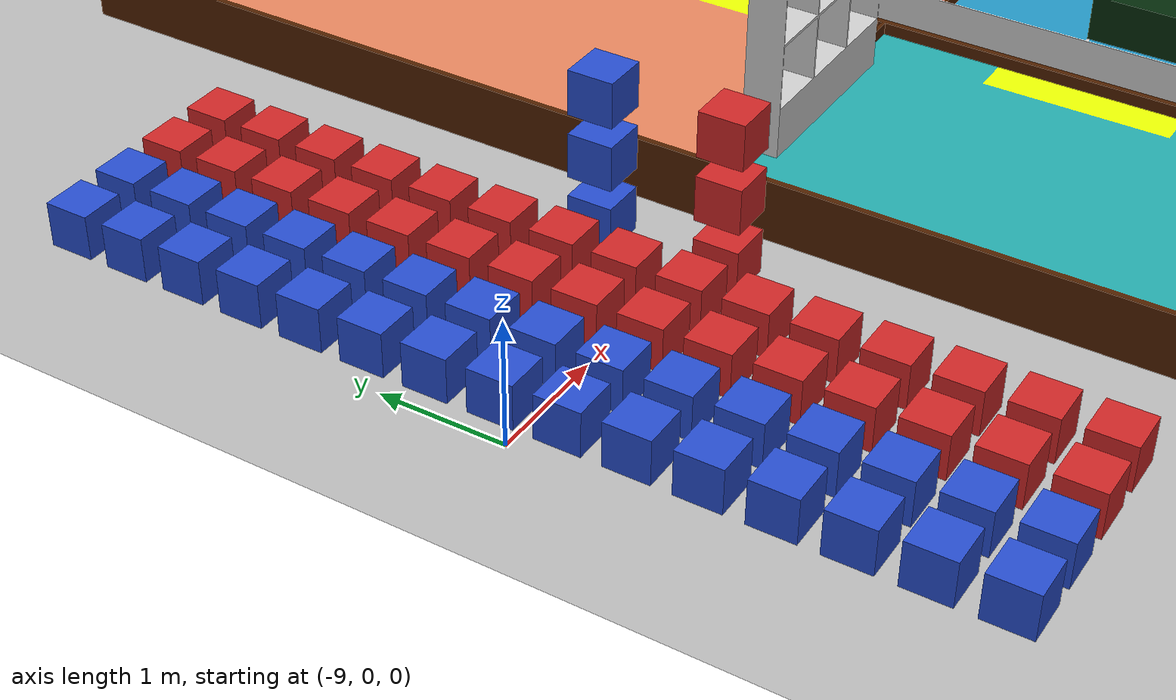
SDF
<sdf version='1.7'>
  <world name='robocon2026_world_scene'>
    <!-- Gazebo ROS State Plugin for set_entity_state service -->
    <plugin name="gazebo_ros_state" filename="libgazebo_ros_state.so">
      <ros>
        <namespace>/</namespace>
      </ros>
      <update_rate>50.0</update_rate>
    </plugin>
    <light name='sun_main1' type='directional'>
      <pose>0 0 20 0 -0 0</pose>
      <diffuse>255 255 255 1</diffuse>
      <specular>0.3 0.3 0.3 1</specular>
      <direction>0.5 0.5 -1</direction>
      <cast_shadows>1</cast_shadows>
      <attenuation>
        <range>1000</range>
        <constant>0.01</constant>
        <linear>0.001</linear>
        <quadratic>0.00</quadratic>
      </attenuation>
    </light>
    <light name='sun_main2' type='directional'>
      <pose>0 0 20 0 -0 0</pose>
      <diffuse>255 255 255 1</diffuse>
      <specular>0.3 0.3 0.3 1</specular>
      <direction>-0.5 0.5 -1</direction>
      <cast_shadows>1</cast_shadows>
      <attenuation>
        <range>1000</range>
        <constant>0.01</constant>
        <linear>0.001</linear>
        <quadratic>0.00</quadratic>
      </attenuation>
    </light>
    <light name='sun_main3' type='directional'>
      <pose>0 0 20 0 -0 0</pose>
      <diffuse>255 255 255 1</diffuse>
      <specular>0.3 0.3 0.3 1</specular>
      <direction>0.5 -0.5 -1</direction>
      <cast_shadows>1</cast_shadows>
      <attenuation>
        <range>1000</range>
        <constant>0.01</constant>
        <linear>0.001</linear>
        <quadratic>0.00</quadratic>
      </attenuation>
    </light>
    <light name='sun_main4' type='directional'>
      <pose>0 0 20 0 -0 0</pose>
      <diffuse>255 255 255 1</diffuse>
      <specular>0.3 0.3 0.3 1</specular>
      <direction>-0.5 -0.5 -1</direction>
      <cast_shadows>1</cast_shadows>
      <attenuation>
        <range>1000</range>
        <constant>0.01</constant>
        <linear>0.001</linear>
        <quadratic>0.00</quadratic>
      </attenuation>
    </light>
    <scene>
      <ambient>0.2 0.2 0.2 1</ambient>
      <background>0.4 0.4 0.4 1</background>
      <shadows>1</shadows>
    </scene>
    <include>
      <uri>model://robocon2026_world</uri>
      <name>robocon2026_field</name>
      <pose>0 0 0.01 0 -0 0</pose>
      <static>true</static>
    </include>
    <include>
      <uri>model://RedR1KFS</uri>
      <name>RedR1KFS</name>
      <pose>-7.0 -0.5 0.5 0 0 0</pose>
    </include>
    <include>
      <uri>model://RedR1KFS</uri>
      <name>RedR1KFS_2</name>
      <pose>-7.0 -0.5 1.0 0 0 0</pose>
    </include>
    <include>
      <uri>model://RedR1KFS</uri>
      <name>RedR1KFS_3</name>
      <pose>-7.0 -0.5 1.5 0 0 0</pose>
    </include>
    <include>
      <uri>model://BlueR1KFS</uri>
      <name>BlueR1KFS</name>
      <pose>-7.0 0.5 0.5 0 0 0</pose>
    </include>
    <include>
      <uri>model://BlueR1KFS</uri>
      <name>BlueR1KFS_2</name>
      <pose>-7.0 0.5 1.0 0 0 0</pose>
    </include>
    <include>
      <uri>model://BlueR1KFS</uri>
      <name>BlueR1KFS_3</name>
      <pose>-7.0 0.5 1.5 0 0 0</pose>
    </include>
    <include>
      <uri>model://RedTrueKFS01</uri>
      <name>RedTrueKFS01</name>
      <pose>-7.5 -3.50 0.5 0 0 0</pose>
    </include>
    <include>
      <uri>model://RedTrueKFS02</uri>
      <name>RedTrueKFS02</name>
      <pose>-7.5 -3.00 0.5 0 0 0</pose>
    </include>
    <include>
      <uri>model://RedTrueKFS03</uri>
      <name>RedTrueKFS03</name>
      <pose>-7.5 -2.50 0.5 0 0 0</pose>
    </include>
    <include>
      <uri>model://RedTrueKFS04</uri>
      <name>RedTrueKFS04</name>
      <pose>-7.5 -2.00 0.5 0 0 0</pose>
    </include>
    <include>
      <uri>model://RedTrueKFS05</uri>
      <name>RedTrueKFS05</name>
      <pose>-7.5 -1.50 0.5 0 0 0</pose>
    </include>
    <include>
      <uri>model://RedTrueKFS06</uri>
      <name>RedTrueKFS06</name>
      <pose>-7.5 -1.00 0.5 0 0 0</pose>
    </include>
    <include>
      <uri>model://RedTrueKFS07</uri>
      <name>RedTrueKFS07</name>
      <pose>-7.5 -0.50 0.5 0 0 0</pose>
    </include>
    <include>
      <uri>model://RedTrueKFS08</uri>
      <name>RedTrueKFS08</name>
      <pose>-7.5 0.00 0.5 0 0 0</pose>
    </include>
    <include>
      <uri>model://RedTrueKFS09</uri>
      <name>RedTrueKFS09</name>
      <pose>-7.5 0.50 0.5 0 0 0</pose>
    </include>
    <include>
      <uri>model://RedTrueKFS10</uri>
      <name>RedTrueKFS10</name>
      <pose>-7.5 1.00 0.5 0 0 0</pose>
    </include>
    <include>
      <uri>model://RedTrueKFS11</uri>
      <name>RedTrueKFS11</name>
      <pose>-7.5 1.50 0.5 0 0 0</pose>
    </include>
    <include>
      <uri>model://RedTrueKFS12</uri>
      <name>RedTrueKFS12</name>
      <pose>-7.5 2.00 0.5 0 0 0</pose>
    </include>
    <include>
      <uri>model://RedTrueKFS13</uri>
      <name>RedTrueKFS13</name>
      <pose>-7.5 2.50 0.5 0 0 0</pose>
    </include>
    <include>
      <uri>model://RedTrueKFS14</uri>
      <name>RedTrueKFS14</name>
      <pose>-7.5 3.00 0.5 0 0 0</pose>
    </include>
    <include>
      <uri>model://RedTrueKFS15</uri>
      <name>RedTrueKFS15</name>
      <pose>-7.5 3.50 0.5 0 0 0</pose>
    </include>
    <include>
      <uri>model://RedFakeKFS01</uri>
      <name>RedFakeKFS01</name>
      <pose>-8.0 -3.50 0.5 0 0 0</pose>
    </include>
    <include>
      <uri>model://RedFakeKFS02</uri>
      <name>RedFakeKFS02</name>
      <pose>-8.0 -3.00 0.5 0 0 0</pose>
    </include>
    <include>
      <uri>model://RedFakeKFS03</uri>
      <name>RedFakeKFS03</name>
      <pose>-8.0 -2.50 0.5 0 0 0</pose>
    </include>
    <include>
      <uri>model://RedFakeKFS04</uri>
      <name>RedFakeKFS04</name>
      <pose>-8.0 -2.00 0.5 0 0 0</pose>
    </include>
    <include>
      <uri>model://RedFakeKFS05</uri>
      <name>RedFakeKFS05</name>
      <pose>-8.0 -1.50 0.5 0 0 0</pose>
    </include>
    <include>
      <uri>model://RedFakeKFS06</uri>
      <name>RedFakeKFS06</name>
      <pose>-8.0 -1.00 0.5 0 0 0</pose>
    </include>
    <include>
      <uri>model://RedFakeKFS07</uri>
      <name>RedFakeKFS07</name>
      <pose>-8.0 -0.50 0.5 0 0 0</pose>
    </include>
    <include>
      <uri>model://RedFakeKFS08</uri>
      <name>RedFakeKFS08</name>
      <pose>-8.0 0.00 0.5 0 0 0</pose>
    </include>
    <include>
      <uri>model://RedFakeKFS09</uri>
      <name>RedFakeKFS09</name>
      <pose>-8.0 0.50 0.5 0 0 0</pose>
    </include>
    <include>
      <uri>model://RedFakeKFS10</uri>
      <name>RedFakeKFS10</name>
      <pose>-8.0 1.00 0.5 0 0 0</pose>
    </include>
    <include>
      <uri>model://RedFakeKFS11</uri>
      <name>RedFakeKFS11</name>
      <pose>-8.0 1.50 0.5 0 0 0</pose>
    </include>
    <include>
      <uri>model://RedFakeKFS12</uri>
      <name>RedFakeKFS12</name>
      <pose>-8.0 2.00 0.5 0 0 0</pose>
    </include>
    <include>
      <uri>model://RedFakeKFS13</uri>
      <name>RedFakeKFS13</name>
      <pose>-8.0 2.50 0.5 0 0 0</pose>
    </include>
    <include>
      <uri>model://RedFakeKFS14</uri>
      <name>RedFakeKFS14</name>
      <pose>-8.0 3.00 0.5 0 0 0</pose>
    </include>
    <include>
      <uri>model://RedFakeKFS15</uri>
      <name>RedFakeKFS15</name>
      <pose>-8.0 3.50 0.5 0 0 0</pose>
    </include>
    <include>
      <uri>model://BlueTrueKFS01</uri>
      <name>BlueTrueKFS01</name>
      <pose>-8.5 -3.50 0.5 0 0 0</pose>
    </include>
    <include>
      <uri>model://BlueTrueKFS02</uri>
      <name>BlueTrueKFS02</name>
      <pose>-8.5 -3.00 0.5 0 0 0</pose>
    </include>
    <include>
      <uri>model://BlueTrueKFS03</uri>
      <name>BlueTrueKFS03</name>
      <pose>-8.5 -2.50 0.5 0 0 0</pose>
    </include>
    <include>
      <uri>model://BlueTrueKFS04</uri>
      <name>BlueTrueKFS04</name>
      <pose>-8.5 -2.00 0.5 0 0 0</pose>
    </include>
    <include>
      <uri>model://BlueTrueKFS05</uri>
      <name>BlueTrueKFS05</name>
      <pose>-8.5 -1.50 0.5 0 0 0</pose>
    </include>
    <include>
      <uri>model://BlueTrueKFS06</uri>
      <name>BlueTrueKFS06</name>
      <pose>-8.5 -1.00 0.5 0 0 0</pose>
    </include>
    <include>
      <uri>model://BlueTrueKFS07</uri>
      <name>BlueTrueKFS07</name>
      <pose>-8.5 -0.50 0.5 0 0 0</pose>
    </include>
    <include>
      <uri>model://BlueTrueKFS08</uri>
      <name>BlueTrueKFS08</name>
      <pose>-8.5 0.00 0.5 0 0 0</pose>
    </include>
    <include>
      <uri>model://BlueTrueKFS09</uri>
      <name>BlueTrueKFS09</name>
      <pose>-8.5 0.50 0.5 0 0 0</pose>
    </include>
    <include>
      <uri>model://BlueTrueKFS10</uri>
      <name>BlueTrueKFS10</name>
      <pose>-8.5 1.00 0.5 0 0 0</pose>
    </include>
    <include>
      <uri>model://BlueTrueKFS11</uri>
      <name>BlueTrueKFS11</name>
      <pose>-8.5 1.50 0.5 0 0 0</pose>
    </include>
    <include>
      <uri>model://BlueTrueKFS12</uri>
      <name>BlueTrueKFS12</name>
      <pose>-8.5 2.00 0.5 0 0 0</pose>
    </include>
    <include>
      <uri>model://BlueTrueKFS13</uri>
      <name>BlueTrueKFS13</name>
      <pose>-8.5 2.50 0.5 0 0 0</pose>
    </include>
    <include>
      <uri>model://BlueTrueKFS14</uri>
      <name>BlueTrueKFS14</name>
      <pose>-8.5 3.00 0.5 0 0 0</pose>
    </include>
    <include>
      <uri>model://BlueTrueKFS15</uri>
      <name>BlueTrueKFS15</name>
      <pose>-8.5 3.50 0.5 0 0 0</pose>
    </include>
    <include>
      <uri>model://BlueFakeKFS01</uri>
      <name>BlueFakeKFS01</name>
      <pose>-9.0 -3.50 0.5 0 0 0</pose>
    </include>
    <include>
      <uri>model://BlueFakeKFS02</uri>
      <name>BlueFakeKFS02</name>
      <pose>-9.0 -3.00 0.5 0 0 0</pose>
    </include>
    <include>
      <uri>model://BlueFakeKFS03</uri>
      <name>BlueFakeKFS03</name>
      <pose>-9.0 -2.50 0.5 0 0 0</pose>
    </include>
    <include>
      <uri>model://BlueFakeKFS04</uri>
      <name>BlueFakeKFS04</name>
      <pose>-9.0 -2.00 0.5 0 0 0</pose>
    </include>
    <include>
      <uri>model://BlueFakeKFS05</uri>
      <name>BlueFakeKFS05</name>
      <pose>-9.0 -1.50 0.5 0 0 0</pose>
    </include>
    <include>
      <uri>model://BlueFakeKFS06</uri>
      <name>BlueFakeKFS06</name>
      <pose>-9.0 -1.00 0.5 0 0 0</pose>
    </include>
    <include>
      <uri>model://BlueFakeKFS07</uri>
      <name>BlueFakeKFS07</name>
      <pose>-9.0 -0.50 0.5 0 0 0</pose>
    </include>
    <include>
      <uri>model://BlueFakeKFS08</uri>
      <name>BlueFakeKFS08</name>
      <pose>-9.0 0.00 0.5 0 0 0</pose>
    </include>
    <include>
      <uri>model://BlueFakeKFS09</uri>
      <name>BlueFakeKFS09</name>
      <pose>-9.0 0.50 0.5 0 0 0</pose>
    </include>
    <include>
      <uri>model://BlueFakeKFS10</uri>
      <name>BlueFakeKFS10</name>
      <pose>-9.0 1.00 0.5 0 0 0</pose>
    </include>
    <include>
      <uri>model://BlueFakeKFS11</uri>
      <name>BlueFakeKFS11</name>
      <pose>-9.0 1.50 0.5 0 0 0</pose>
    </include>
    <include>
      <uri>model://BlueFakeKFS12</uri>
      <name>BlueFakeKFS12</name>
      <pose>-9.0 2.00 0.5 0 0 0</pose>
    </include>
    <include>
      <uri>model://BlueFakeKFS13</uri>
      <name>BlueFakeKFS13</name>
      <pose>-9.0 2.50 0.5 0 0 0</pose>
    </include>
    <include>
      <uri>model://BlueFakeKFS14</uri>
      <name>BlueFakeKFS14</name>
      <pose>-9.0 3.00 0.5 0 0 0</pose>
    </include>
    <include>
      <uri>model://BlueFakeKFS15</uri>
      <name>BlueFakeKFS15</name>
      <pose>-9.0 3.50 0.5 0 0 0</pose>
    </include>

</world>
</sdf>

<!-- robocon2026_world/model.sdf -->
<sdf version="1.7">
  <model name="robocon2026_world">
    <static>true</static>
    <link name="arena_link">
      <collision name="arena_collision">
        <geometry>
          <mesh>
            <uri>model://robocon2026_world/meshes/robocon2026.dae</uri>
          </mesh>
        </geometry>
        <max_contacts>10</max_contacts>
        <surface>
          <contact>
            <ode/>
          </contact>
          <bounce/>
          <friction>
            <torsional>
              <ode/>
            </torsional>
            <ode/>
          </friction>
        </surface>
      </collision>
      <visual name="arena_visual">
        <geometry>
          <mesh>
            <uri>model://robocon2026_world/meshes/robocon2026.dae</uri>
          </mesh>
        </geometry>
      </visual>
      <self_collide>0</self_collide>
      <enable_wind>0</enable_wind>
      <kinematic>0</kinematic>
    </link>
  </model>
</sdf>

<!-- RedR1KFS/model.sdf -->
<sdf version="1.6">
  <model name="RedR1KFS">
    <static>false</static>
    <link name="link">
      <inertial>
        <mass>1.0</mass>
        <inertia>
          <ixx>0.083</ixx> <ixy>0.0</ixy> <ixz>0.0</ixz>
          <iyy>0.083</iyy> <iyz>0.0</iyz>
          <izz>0.083</izz>
        </inertia>
      </inertial>
      <collision name="collision">
        <geometry>
          <box><size>0.35 0.35 0.35</size></box>
        </geometry>
      </collision>
      <visual name="visual">
        <geometry>
          <mesh>
            <uri>model://RedR1KFS/meshes/model.obj</uri>
            <scale>1 1 1</scale>
          </mesh>
        </geometry>
        <material>
          <script>
            <uri>model://RedR1KFS/materials/scripts</uri>
            <uri>model://RedR1KFS/materials/textures</uri>
            <name>RoboCon/RedR1KFS</name>
          </script>
        </material>
      </visual>
    </link>
  </model>
</sdf>

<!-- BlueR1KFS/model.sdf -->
<sdf version="1.6">
  <model name="BlueR1KFS">
    <static>false</static>
    <link name="link">
      <inertial>
        <mass>1.0</mass>
        <inertia>
          <ixx>0.083</ixx> <ixy>0.0</ixy> <ixz>0.0</ixz>
          <iyy>0.083</iyy> <iyz>0.0</iyz>
          <izz>0.083</izz>
        </inertia>
      </inertial>
      <collision name="collision">
        <geometry>
          <box><size>0.35 0.35 0.35</size></box>
        </geometry>
      </collision>
      <visual name="visual">
        <geometry>
          <mesh>
            <uri>model://BlueR1KFS/meshes/model.obj</uri>
            <scale>1 1 1</scale>
          </mesh>
        </geometry>
        <material>
          <script>
            <uri>model://BlueR1KFS/materials/scripts</uri>
            <uri>model://BlueR1KFS/materials/textures</uri>
            <name>RoboCon/BlueR1KFS</name>
          </script>
        </material>
      </visual>
    </link>
  </model>
</sdf>

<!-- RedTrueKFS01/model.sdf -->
<sdf version="1.6">
  <model name="RedTrueKFS01">
    <static>false</static>
    <link name="link">
      <inertial>
        <mass>1.0</mass>
        <inertia>
          <ixx>0.083</ixx> <ixy>0.0</ixy> <ixz>0.0</ixz>
          <iyy>0.083</iyy> <iyz>0.0</iyz>
          <izz>0.083</izz>
        </inertia>
      </inertial>
      <collision name="collision">
        <geometry>
          <box><size>0.35 0.35 0.35</size></box>
        </geometry>
      </collision>
      <visual name="visual">
        <geometry>
          <mesh>
            <uri>model://RedTrueKFS01/meshes/model.obj</uri>
            <scale>1 1 1</scale>
          </mesh>
        </geometry>
        <material>
          <script>
            <uri>model://RedTrueKFS01/materials/scripts</uri>
            <uri>model://RedTrueKFS01/materials/textures</uri>
            <name>RoboCon/RedTrueKFS01</name>
          </script>
        </material>
      </visual>
    </link>
  </model>
</sdf>

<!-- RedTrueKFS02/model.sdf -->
<sdf version="1.6">
  <model name="RedTrueKFS02">
    <static>false</static>
    <link name="link">
      <inertial>
        <mass>1.0</mass>
        <inertia>
          <ixx>0.083</ixx> <ixy>0.0</ixy> <ixz>0.0</ixz>
          <iyy>0.083</iyy> <iyz>0.0</iyz>
          <izz>0.083</izz>
        </inertia>
      </inertial>
      <collision name="collision">
        <geometry>
          <box><size>0.35 0.35 0.35</size></box>
        </geometry>
      </collision>
      <visual name="visual">
        <geometry>
          <mesh>
            <uri>model://RedTrueKFS02/meshes/model.obj</uri>
            <scale>1 1 1</scale>
          </mesh>
        </geometry>
        <material>
          <script>
            <uri>model://RedTrueKFS02/materials/scripts</uri>
            <uri>model://RedTrueKFS02/materials/textures</uri>
            <name>RoboCon/RedTrueKFS02</name>
          </script>
        </material>
      </visual>
    </link>
  </model>
</sdf>

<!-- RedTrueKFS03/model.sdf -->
<sdf version="1.6">
  <model name="RedTrueKFS03">
    <static>false</static>
    <link name="link">
      <inertial>
        <mass>1.0</mass>
        <inertia>
          <ixx>0.083</ixx> <ixy>0.0</ixy> <ixz>0.0</ixz>
          <iyy>0.083</iyy> <iyz>0.0</iyz>
          <izz>0.083</izz>
        </inertia>
      </inertial>
      <collision name="collision">
        <geometry>
          <box><size>0.35 0.35 0.35</size></box>
        </geometry>
      </collision>
      <visual name="visual">
        <geometry>
          <mesh>
            <uri>model://RedTrueKFS03/meshes/model.obj</uri>
            <scale>1 1 1</scale>
          </mesh>
        </geometry>
        <material>
          <script>
            <uri>model://RedTrueKFS03/materials/scripts</uri>
            <uri>model://RedTrueKFS03/materials/textures</uri>
            <name>RoboCon/RedTrueKFS03</name>
          </script>
        </material>
      </visual>
    </link>
  </model>
</sdf>

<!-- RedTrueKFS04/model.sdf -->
<sdf version="1.6">
  <model name="RedTrueKFS04">
    <static>false</static>
    <link name="link">
      <inertial>
        <mass>1.0</mass>
        <inertia>
          <ixx>0.083</ixx> <ixy>0.0</ixy> <ixz>0.0</ixz>
          <iyy>0.083</iyy> <iyz>0.0</iyz>
          <izz>0.083</izz>
        </inertia>
      </inertial>
      <collision name="collision">
        <geometry>
          <box><size>0.35 0.35 0.35</size></box>
        </geometry>
      </collision>
      <visual name="visual">
        <geometry>
          <mesh>
            <uri>model://RedTrueKFS04/meshes/model.obj</uri>
            <scale>1 1 1</scale>
          </mesh>
        </geometry>
        <material>
          <script>
            <uri>model://RedTrueKFS04/materials/scripts</uri>
            <uri>model://RedTrueKFS04/materials/textures</uri>
            <name>RoboCon/RedTrueKFS04</name>
          </script>
        </material>
      </visual>
    </link>
  </model>
</sdf>

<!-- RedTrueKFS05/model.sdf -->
<sdf version="1.6">
  <model name="RedTrueKFS05">
    <static>false</static>
    <link name="link">
      <inertial>
        <mass>1.0</mass>
        <inertia>
          <ixx>0.083</ixx> <ixy>0.0</ixy> <ixz>0.0</ixz>
          <iyy>0.083</iyy> <iyz>0.0</iyz>
          <izz>0.083</izz>
        </inertia>
      </inertial>
      <collision name="collision">
        <geometry>
          <box><size>0.35 0.35 0.35</size></box>
        </geometry>
      </collision>
      <visual name="visual">
        <geometry>
          <mesh>
            <uri>model://RedTrueKFS05/meshes/model.obj</uri>
            <scale>1 1 1</scale>
          </mesh>
        </geometry>
        <material>
          <script>
            <uri>model://RedTrueKFS05/materials/scripts</uri>
            <uri>model://RedTrueKFS05/materials/textures</uri>
            <name>RoboCon/RedTrueKFS05</name>
          </script>
        </material>
      </visual>
    </link>
  </model>
</sdf>

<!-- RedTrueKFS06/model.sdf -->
<sdf version="1.6">
  <model name="RedTrueKFS06">
    <static>false</static>
    <link name="link">
      <inertial>
        <mass>1.0</mass>
        <inertia>
          <ixx>0.083</ixx> <ixy>0.0</ixy> <ixz>0.0</ixz>
          <iyy>0.083</iyy> <iyz>0.0</iyz>
          <izz>0.083</izz>
        </inertia>
      </inertial>
      <collision name="collision">
        <geometry>
          <box><size>0.35 0.35 0.35</size></box>
        </geometry>
      </collision>
      <visual name="visual">
        <geometry>
          <mesh>
            <uri>model://RedTrueKFS06/meshes/model.obj</uri>
            <scale>1 1 1</scale>
          </mesh>
        </geometry>
        <material>
          <script>
            <uri>model://RedTrueKFS06/materials/scripts</uri>
            <uri>model://RedTrueKFS06/materials/textures</uri>
            <name>RoboCon/RedTrueKFS06</name>
          </script>
        </material>
      </visual>
    </link>
  </model>
</sdf>

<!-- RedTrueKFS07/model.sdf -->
<sdf version="1.6">
  <model name="RedTrueKFS07">
    <static>false</static>
    <link name="link">
      <inertial>
        <mass>1.0</mass>
        <inertia>
          <ixx>0.083</ixx> <ixy>0.0</ixy> <ixz>0.0</ixz>
          <iyy>0.083</iyy> <iyz>0.0</iyz>
          <izz>0.083</izz>
        </inertia>
      </inertial>
      <collision name="collision">
        <geometry>
          <box><size>0.35 0.35 0.35</size></box>
        </geometry>
      </collision>
      <visual name="visual">
        <geometry>
          <mesh>
            <uri>model://RedTrueKFS07/meshes/model.obj</uri>
            <scale>1 1 1</scale>
          </mesh>
        </geometry>
        <material>
          <script>
            <uri>model://RedTrueKFS07/materials/scripts</uri>
            <uri>model://RedTrueKFS07/materials/textures</uri>
            <name>RoboCon/RedTrueKFS07</name>
          </script>
        </material>
      </visual>
    </link>
  </model>
</sdf>

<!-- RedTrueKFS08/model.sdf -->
<sdf version="1.6">
  <model name="RedTrueKFS08">
    <static>false</static>
    <link name="link">
      <inertial>
        <mass>1.0</mass>
        <inertia>
          <ixx>0.083</ixx> <ixy>0.0</ixy> <ixz>0.0</ixz>
          <iyy>0.083</iyy> <iyz>0.0</iyz>
          <izz>0.083</izz>
        </inertia>
      </inertial>
      <collision name="collision">
        <geometry>
          <box><size>0.35 0.35 0.35</size></box>
        </geometry>
      </collision>
      <visual name="visual">
        <geometry>
          <mesh>
            <uri>model://RedTrueKFS08/meshes/model.obj</uri>
            <scale>1 1 1</scale>
          </mesh>
        </geometry>
        <material>
          <script>
            <uri>model://RedTrueKFS08/materials/scripts</uri>
            <uri>model://RedTrueKFS08/materials/textures</uri>
            <name>RoboCon/RedTrueKFS08</name>
          </script>
        </material>
      </visual>
    </link>
  </model>
</sdf>

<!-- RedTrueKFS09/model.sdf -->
<sdf version="1.6">
  <model name="RedTrueKFS09">
    <static>false</static>
    <link name="link">
      <inertial>
        <mass>1.0</mass>
        <inertia>
          <ixx>0.083</ixx> <ixy>0.0</ixy> <ixz>0.0</ixz>
          <iyy>0.083</iyy> <iyz>0.0</iyz>
          <izz>0.083</izz>
        </inertia>
      </inertial>
      <collision name="collision">
        <geometry>
          <box><size>0.35 0.35 0.35</size></box>
        </geometry>
      </collision>
      <visual name="visual">
        <geometry>
          <mesh>
            <uri>model://RedTrueKFS09/meshes/model.obj</uri>
            <scale>1 1 1</scale>
          </mesh>
        </geometry>
        <material>
          <script>
            <uri>model://RedTrueKFS09/materials/scripts</uri>
            <uri>model://RedTrueKFS09/materials/textures</uri>
            <name>RoboCon/RedTrueKFS09</name>
          </script>
        </material>
      </visual>
    </link>
  </model>
</sdf>

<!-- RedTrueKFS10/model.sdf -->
<sdf version="1.6">
  <model name="RedTrueKFS10">
    <static>false</static>
    <link name="link">
      <inertial>
        <mass>1.0</mass>
        <inertia>
          <ixx>0.083</ixx> <ixy>0.0</ixy> <ixz>0.0</ixz>
          <iyy>0.083</iyy> <iyz>0.0</iyz>
          <izz>0.083</izz>
        </inertia>
      </inertial>
      <collision name="collision">
        <geometry>
          <box><size>0.35 0.35 0.35</size></box>
        </geometry>
      </collision>
      <visual name="visual">
        <geometry>
          <mesh>
            <uri>model://RedTrueKFS10/meshes/model.obj</uri>
            <scale>1 1 1</scale>
          </mesh>
        </geometry>
        <material>
          <script>
            <uri>model://RedTrueKFS10/materials/scripts</uri>
            <uri>model://RedTrueKFS10/materials/textures</uri>
            <name>RoboCon/RedTrueKFS10</name>
          </script>
        </material>
      </visual>
    </link>
  </model>
</sdf>

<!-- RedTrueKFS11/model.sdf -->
<sdf version="1.6">
  <model name="RedTrueKFS11">
    <static>false</static>
    <link name="link">
      <inertial>
        <mass>1.0</mass>
        <inertia>
          <ixx>0.083</ixx> <ixy>0.0</ixy> <ixz>0.0</ixz>
          <iyy>0.083</iyy> <iyz>0.0</iyz>
          <izz>0.083</izz>
        </inertia>
      </inertial>
      <collision name="collision">
        <geometry>
          <box><size>0.35 0.35 0.35</size></box>
        </geometry>
      </collision>
      <visual name="visual">
        <geometry>
          <mesh>
            <uri>model://RedTrueKFS11/meshes/model.obj</uri>
            <scale>1 1 1</scale>
          </mesh>
        </geometry>
        <material>
          <script>
            <uri>model://RedTrueKFS11/materials/scripts</uri>
            <uri>model://RedTrueKFS11/materials/textures</uri>
            <name>RoboCon/RedTrueKFS11</name>
          </script>
        </material>
      </visual>
    </link>
  </model>
</sdf>

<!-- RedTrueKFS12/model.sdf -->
<sdf version="1.6">
  <model name="RedTrueKFS12">
    <static>false</static>
    <link name="link">
      <inertial>
        <mass>1.0</mass>
        <inertia>
          <ixx>0.083</ixx> <ixy>0.0</ixy> <ixz>0.0</ixz>
          <iyy>0.083</iyy> <iyz>0.0</iyz>
          <izz>0.083</izz>
        </inertia>
      </inertial>
      <collision name="collision">
        <geometry>
          <box><size>0.35 0.35 0.35</size></box>
        </geometry>
      </collision>
      <visual name="visual">
        <geometry>
          <mesh>
            <uri>model://RedTrueKFS12/meshes/model.obj</uri>
            <scale>1 1 1</scale>
          </mesh>
        </geometry>
        <material>
          <script>
            <uri>model://RedTrueKFS12/materials/scripts</uri>
            <uri>model://RedTrueKFS12/materials/textures</uri>
            <name>RoboCon/RedTrueKFS12</name>
          </script>
        </material>
      </visual>
    </link>
  </model>
</sdf>

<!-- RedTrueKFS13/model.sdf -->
<sdf version="1.6">
  <model name="RedTrueKFS13">
    <static>false</static>
    <link name="link">
      <inertial>
        <mass>1.0</mass>
        <inertia>
          <ixx>0.083</ixx> <ixy>0.0</ixy> <ixz>0.0</ixz>
          <iyy>0.083</iyy> <iyz>0.0</iyz>
          <izz>0.083</izz>
        </inertia>
      </inertial>
      <collision name="collision">
        <geometry>
          <box><size>0.35 0.35 0.35</size></box>
        </geometry>
      </collision>
      <visual name="visual">
        <geometry>
          <mesh>
            <uri>model://RedTrueKFS13/meshes/model.obj</uri>
            <scale>1 1 1</scale>
          </mesh>
        </geometry>
        <material>
          <script>
            <uri>model://RedTrueKFS13/materials/scripts</uri>
            <uri>model://RedTrueKFS13/materials/textures</uri>
            <name>RoboCon/RedTrueKFS13</name>
          </script>
        </material>
      </visual>
    </link>
  </model>
</sdf>

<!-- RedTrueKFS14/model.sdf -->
<sdf version="1.6">
  <model name="RedTrueKFS14">
    <static>false</static>
    <link name="link">
      <inertial>
        <mass>1.0</mass>
        <inertia>
          <ixx>0.083</ixx> <ixy>0.0</ixy> <ixz>0.0</ixz>
          <iyy>0.083</iyy> <iyz>0.0</iyz>
          <izz>0.083</izz>
        </inertia>
      </inertial>
      <collision name="collision">
        <geometry>
          <box><size>0.35 0.35 0.35</size></box>
        </geometry>
      </collision>
      <visual name="visual">
        <geometry>
          <mesh>
            <uri>model://RedTrueKFS14/meshes/model.obj</uri>
            <scale>1 1 1</scale>
          </mesh>
        </geometry>
        <material>
          <script>
            <uri>model://RedTrueKFS14/materials/scripts</uri>
            <uri>model://RedTrueKFS14/materials/textures</uri>
            <name>RoboCon/RedTrueKFS14</name>
          </script>
        </material>
      </visual>
    </link>
  </model>
</sdf>

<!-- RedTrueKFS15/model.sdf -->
<sdf version="1.6">
  <model name="RedTrueKFS15">
    <static>false</static>
    <link name="link">
      <inertial>
        <mass>1.0</mass>
        <inertia>
          <ixx>0.083</ixx> <ixy>0.0</ixy> <ixz>0.0</ixz>
          <iyy>0.083</iyy> <iyz>0.0</iyz>
          <izz>0.083</izz>
        </inertia>
      </inertial>
      <collision name="collision">
        <geometry>
          <box><size>0.35 0.35 0.35</size></box>
        </geometry>
      </collision>
      <visual name="visual">
        <geometry>
          <mesh>
            <uri>model://RedTrueKFS15/meshes/model.obj</uri>
            <scale>1 1 1</scale>
          </mesh>
        </geometry>
        <material>
          <script>
            <uri>model://RedTrueKFS15/materials/scripts</uri>
            <uri>model://RedTrueKFS15/materials/textures</uri>
            <name>RoboCon/RedTrueKFS15</name>
          </script>
        </material>
      </visual>
    </link>
  </model>
</sdf>

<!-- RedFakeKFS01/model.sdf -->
<sdf version="1.6">
  <model name="RedFakeKFS01">
    <static>false</static>
    <link name="link">
      <inertial>
        <mass>1.0</mass>
        <inertia>
          <ixx>0.083</ixx> <ixy>0.0</ixy> <ixz>0.0</ixz>
          <iyy>0.083</iyy> <iyz>0.0</iyz>
          <izz>0.083</izz>
        </inertia>
      </inertial>
      <collision name="collision">
        <geometry>
          <box><size>0.35 0.35 0.35</size></box>
        </geometry>
      </collision>
      <visual name="visual">
        <geometry>
          <mesh>
            <uri>model://RedFakeKFS01/meshes/model.obj</uri>
            <scale>1 1 1</scale>
          </mesh>
        </geometry>
        <material>
          <script>
            <uri>model://RedFakeKFS01/materials/scripts</uri>
            <uri>model://RedFakeKFS01/materials/textures</uri>
            <name>RoboCon/RedFakeKFS01</name>
          </script>
        </material>
      </visual>
    </link>
  </model>
</sdf>

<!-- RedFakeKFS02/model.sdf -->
<sdf version="1.6">
  <model name="RedFakeKFS02">
    <static>false</static>
    <link name="link">
      <inertial>
        <mass>1.0</mass>
        <inertia>
          <ixx>0.083</ixx> <ixy>0.0</ixy> <ixz>0.0</ixz>
          <iyy>0.083</iyy> <iyz>0.0</iyz>
          <izz>0.083</izz>
        </inertia>
      </inertial>
      <collision name="collision">
        <geometry>
          <box><size>0.35 0.35 0.35</size></box>
        </geometry>
      </collision>
      <visual name="visual">
        <geometry>
          <mesh>
            <uri>model://RedFakeKFS02/meshes/model.obj</uri>
            <scale>1 1 1</scale>
          </mesh>
        </geometry>
        <material>
          <script>
            <uri>model://RedFakeKFS02/materials/scripts</uri>
            <uri>model://RedFakeKFS02/materials/textures</uri>
            <name>RoboCon/RedFakeKFS02</name>
          </script>
        </material>
      </visual>
    </link>
  </model>
</sdf>

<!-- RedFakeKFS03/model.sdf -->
<sdf version="1.6">
  <model name="RedFakeKFS03">
    <static>false</static>
    <link name="link">
      <inertial>
        <mass>1.0</mass>
        <inertia>
          <ixx>0.083</ixx> <ixy>0.0</ixy> <ixz>0.0</ixz>
          <iyy>0.083</iyy> <iyz>0.0</iyz>
          <izz>0.083</izz>
        </inertia>
      </inertial>
      <collision name="collision">
        <geometry>
          <box><size>0.35 0.35 0.35</size></box>
        </geometry>
      </collision>
      <visual name="visual">
        <geometry>
          <mesh>
            <uri>model://RedFakeKFS03/meshes/model.obj</uri>
            <scale>1 1 1</scale>
          </mesh>
        </geometry>
        <material>
          <script>
            <uri>model://RedFakeKFS03/materials/scripts</uri>
            <uri>model://RedFakeKFS03/materials/textures</uri>
            <name>RoboCon/RedFakeKFS03</name>
          </script>
        </material>
      </visual>
    </link>
  </model>
</sdf>

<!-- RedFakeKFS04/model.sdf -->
<sdf version="1.6">
  <model name="RedFakeKFS04">
    <static>false</static>
    <link name="link">
      <inertial>
        <mass>1.0</mass>
        <inertia>
          <ixx>0.083</ixx> <ixy>0.0</ixy> <ixz>0.0</ixz>
          <iyy>0.083</iyy> <iyz>0.0</iyz>
          <izz>0.083</izz>
        </inertia>
      </inertial>
      <collision name="collision">
        <geometry>
          <box><size>0.35 0.35 0.35</size></box>
        </geometry>
      </collision>
      <visual name="visual">
        <geometry>
          <mesh>
            <uri>model://RedFakeKFS04/meshes/model.obj</uri>
            <scale>1 1 1</scale>
          </mesh>
        </geometry>
        <material>
          <script>
            <uri>model://RedFakeKFS04/materials/scripts</uri>
            <uri>model://RedFakeKFS04/materials/textures</uri>
            <name>RoboCon/RedFakeKFS04</name>
          </script>
        </material>
      </visual>
    </link>
  </model>
</sdf>

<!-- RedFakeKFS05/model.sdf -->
<sdf version="1.6">
  <model name="RedFakeKFS05">
    <static>false</static>
    <link name="link">
      <inertial>
        <mass>1.0</mass>
        <inertia>
          <ixx>0.083</ixx> <ixy>0.0</ixy> <ixz>0.0</ixz>
          <iyy>0.083</iyy> <iyz>0.0</iyz>
          <izz>0.083</izz>
        </inertia>
      </inertial>
      <collision name="collision">
        <geometry>
          <box><size>0.35 0.35 0.35</size></box>
        </geometry>
      </collision>
      <visual name="visual">
        <geometry>
          <mesh>
            <uri>model://RedFakeKFS05/meshes/model.obj</uri>
            <scale>1 1 1</scale>
          </mesh>
        </geometry>
        <material>
          <script>
            <uri>model://RedFakeKFS05/materials/scripts</uri>
            <uri>model://RedFakeKFS05/materials/textures</uri>
            <name>RoboCon/RedFakeKFS05</name>
          </script>
        </material>
      </visual>
    </link>
  </model>
</sdf>

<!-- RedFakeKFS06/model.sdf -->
<sdf version="1.6">
  <model name="RedFakeKFS06">
    <static>false</static>
    <link name="link">
      <inertial>
        <mass>1.0</mass>
        <inertia>
          <ixx>0.083</ixx> <ixy>0.0</ixy> <ixz>0.0</ixz>
          <iyy>0.083</iyy> <iyz>0.0</iyz>
          <izz>0.083</izz>
        </inertia>
      </inertial>
      <collision name="collision">
        <geometry>
          <box><size>0.35 0.35 0.35</size></box>
        </geometry>
      </collision>
      <visual name="visual">
        <geometry>
          <mesh>
            <uri>model://RedFakeKFS06/meshes/model.obj</uri>
            <scale>1 1 1</scale>
          </mesh>
        </geometry>
        <material>
          <script>
            <uri>model://RedFakeKFS06/materials/scripts</uri>
            <uri>model://RedFakeKFS06/materials/textures</uri>
            <name>RoboCon/RedFakeKFS06</name>
          </script>
        </material>
      </visual>
    </link>
  </model>
</sdf>

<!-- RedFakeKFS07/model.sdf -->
<sdf version="1.6">
  <model name="RedFakeKFS07">
    <static>false</static>
    <link name="link">
      <inertial>
        <mass>1.0</mass>
        <inertia>
          <ixx>0.083</ixx> <ixy>0.0</ixy> <ixz>0.0</ixz>
          <iyy>0.083</iyy> <iyz>0.0</iyz>
          <izz>0.083</izz>
        </inertia>
      </inertial>
      <collision name="collision">
        <geometry>
          <box><size>0.35 0.35 0.35</size></box>
        </geometry>
      </collision>
      <visual name="visual">
        <geometry>
          <mesh>
            <uri>model://RedFakeKFS07/meshes/model.obj</uri>
            <scale>1 1 1</scale>
          </mesh>
        </geometry>
        <material>
          <script>
            <uri>model://RedFakeKFS07/materials/scripts</uri>
            <uri>model://RedFakeKFS07/materials/textures</uri>
            <name>RoboCon/RedFakeKFS07</name>
          </script>
        </material>
      </visual>
    </link>
  </model>
</sdf>

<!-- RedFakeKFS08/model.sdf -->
<sdf version="1.6">
  <model name="RedFakeKFS08">
    <static>false</static>
    <link name="link">
      <inertial>
        <mass>1.0</mass>
        <inertia>
          <ixx>0.083</ixx> <ixy>0.0</ixy> <ixz>0.0</ixz>
          <iyy>0.083</iyy> <iyz>0.0</iyz>
          <izz>0.083</izz>
        </inertia>
      </inertial>
      <collision name="collision">
        <geometry>
          <box><size>0.35 0.35 0.35</size></box>
        </geometry>
      </collision>
      <visual name="visual">
        <geometry>
          <mesh>
            <uri>model://RedFakeKFS08/meshes/model.obj</uri>
            <scale>1 1 1</scale>
          </mesh>
        </geometry>
        <material>
          <script>
            <uri>model://RedFakeKFS08/materials/scripts</uri>
            <uri>model://RedFakeKFS08/materials/textures</uri>
            <name>RoboCon/RedFakeKFS08</name>
          </script>
        </material>
      </visual>
    </link>
  </model>
</sdf>

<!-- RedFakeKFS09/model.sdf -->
<sdf version="1.6">
  <model name="RedFakeKFS09">
    <static>false</static>
    <link name="link">
      <inertial>
        <mass>1.0</mass>
        <inertia>
          <ixx>0.083</ixx> <ixy>0.0</ixy> <ixz>0.0</ixz>
          <iyy>0.083</iyy> <iyz>0.0</iyz>
          <izz>0.083</izz>
        </inertia>
      </inertial>
      <collision name="collision">
        <geometry>
          <box><size>0.35 0.35 0.35</size></box>
        </geometry>
      </collision>
      <visual name="visual">
        <geometry>
          <mesh>
            <uri>model://RedFakeKFS09/meshes/model.obj</uri>
            <scale>1 1 1</scale>
          </mesh>
        </geometry>
        <material>
          <script>
            <uri>model://RedFakeKFS09/materials/scripts</uri>
            <uri>model://RedFakeKFS09/materials/textures</uri>
            <name>RoboCon/RedFakeKFS09</name>
          </script>
        </material>
      </visual>
    </link>
  </model>
</sdf>

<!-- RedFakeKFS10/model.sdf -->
<sdf version="1.6">
  <model name="RedFakeKFS10">
    <static>false</static>
    <link name="link">
      <inertial>
        <mass>1.0</mass>
        <inertia>
          <ixx>0.083</ixx> <ixy>0.0</ixy> <ixz>0.0</ixz>
          <iyy>0.083</iyy> <iyz>0.0</iyz>
          <izz>0.083</izz>
        </inertia>
      </inertial>
      <collision name="collision">
        <geometry>
          <box><size>0.35 0.35 0.35</size></box>
        </geometry>
      </collision>
      <visual name="visual">
        <geometry>
          <mesh>
            <uri>model://RedFakeKFS10/meshes/model.obj</uri>
            <scale>1 1 1</scale>
          </mesh>
        </geometry>
        <material>
          <script>
            <uri>model://RedFakeKFS10/materials/scripts</uri>
            <uri>model://RedFakeKFS10/materials/textures</uri>
            <name>RoboCon/RedFakeKFS10</name>
          </script>
        </material>
      </visual>
    </link>
  </model>
</sdf>

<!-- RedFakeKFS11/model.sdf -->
<sdf version="1.6">
  <model name="RedFakeKFS11">
    <static>false</static>
    <link name="link">
      <inertial>
        <mass>1.0</mass>
        <inertia>
          <ixx>0.083</ixx> <ixy>0.0</ixy> <ixz>0.0</ixz>
          <iyy>0.083</iyy> <iyz>0.0</iyz>
          <izz>0.083</izz>
        </inertia>
      </inertial>
      <collision name="collision">
        <geometry>
          <box><size>0.35 0.35 0.35</size></box>
        </geometry>
      </collision>
      <visual name="visual">
        <geometry>
          <mesh>
            <uri>model://RedFakeKFS11/meshes/model.obj</uri>
            <scale>1 1 1</scale>
          </mesh>
        </geometry>
        <material>
          <script>
            <uri>model://RedFakeKFS11/materials/scripts</uri>
            <uri>model://RedFakeKFS11/materials/textures</uri>
            <name>RoboCon/RedFakeKFS11</name>
          </script>
        </material>
      </visual>
    </link>
  </model>
</sdf>

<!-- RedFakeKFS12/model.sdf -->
<sdf version="1.6">
  <model name="RedFakeKFS12">
    <static>false</static>
    <link name="link">
      <inertial>
        <mass>1.0</mass>
        <inertia>
          <ixx>0.083</ixx> <ixy>0.0</ixy> <ixz>0.0</ixz>
          <iyy>0.083</iyy> <iyz>0.0</iyz>
          <izz>0.083</izz>
        </inertia>
      </inertial>
      <collision name="collision">
        <geometry>
          <box><size>0.35 0.35 0.35</size></box>
        </geometry>
      </collision>
      <visual name="visual">
        <geometry>
          <mesh>
            <uri>model://RedFakeKFS12/meshes/model.obj</uri>
            <scale>1 1 1</scale>
          </mesh>
        </geometry>
        <material>
          <script>
            <uri>model://RedFakeKFS12/materials/scripts</uri>
            <uri>model://RedFakeKFS12/materials/textures</uri>
            <name>RoboCon/RedFakeKFS12</name>
          </script>
        </material>
      </visual>
    </link>
  </model>
</sdf>

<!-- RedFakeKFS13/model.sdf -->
<sdf version="1.6">
  <model name="RedFakeKFS13">
    <static>false</static>
    <link name="link">
      <inertial>
        <mass>1.0</mass>
        <inertia>
          <ixx>0.083</ixx> <ixy>0.0</ixy> <ixz>0.0</ixz>
          <iyy>0.083</iyy> <iyz>0.0</iyz>
          <izz>0.083</izz>
        </inertia>
      </inertial>
      <collision name="collision">
        <geometry>
          <box><size>0.35 0.35 0.35</size></box>
        </geometry>
      </collision>
      <visual name="visual">
        <geometry>
          <mesh>
            <uri>model://RedFakeKFS13/meshes/model.obj</uri>
            <scale>1 1 1</scale>
          </mesh>
        </geometry>
        <material>
          <script>
            <uri>model://RedFakeKFS13/materials/scripts</uri>
            <uri>model://RedFakeKFS13/materials/textures</uri>
            <name>RoboCon/RedFakeKFS13</name>
          </script>
        </material>
      </visual>
    </link>
  </model>
</sdf>

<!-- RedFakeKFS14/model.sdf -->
<sdf version="1.6">
  <model name="RedFakeKFS14">
    <static>false</static>
    <link name="link">
      <inertial>
        <mass>1.0</mass>
        <inertia>
          <ixx>0.083</ixx> <ixy>0.0</ixy> <ixz>0.0</ixz>
          <iyy>0.083</iyy> <iyz>0.0</iyz>
          <izz>0.083</izz>
        </inertia>
      </inertial>
      <collision name="collision">
        <geometry>
          <box><size>0.35 0.35 0.35</size></box>
        </geometry>
      </collision>
      <visual name="visual">
        <geometry>
          <mesh>
            <uri>model://RedFakeKFS14/meshes/model.obj</uri>
            <scale>1 1 1</scale>
          </mesh>
        </geometry>
        <material>
          <script>
            <uri>model://RedFakeKFS14/materials/scripts</uri>
            <uri>model://RedFakeKFS14/materials/textures</uri>
            <name>RoboCon/RedFakeKFS14</name>
          </script>
        </material>
      </visual>
    </link>
  </model>
</sdf>

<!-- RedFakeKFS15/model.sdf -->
<sdf version="1.6">
  <model name="RedFakeKFS15">
    <static>false</static>
    <link name="link">
      <inertial>
        <mass>1.0</mass>
        <inertia>
          <ixx>0.083</ixx> <ixy>0.0</ixy> <ixz>0.0</ixz>
          <iyy>0.083</iyy> <iyz>0.0</iyz>
          <izz>0.083</izz>
        </inertia>
      </inertial>
      <collision name="collision">
        <geometry>
          <box><size>0.35 0.35 0.35</size></box>
        </geometry>
      </collision>
      <visual name="visual">
        <geometry>
          <mesh>
            <uri>model://RedFakeKFS15/meshes/model.obj</uri>
            <scale>1 1 1</scale>
          </mesh>
        </geometry>
        <material>
          <script>
            <uri>model://RedFakeKFS15/materials/scripts</uri>
            <uri>model://RedFakeKFS15/materials/textures</uri>
            <name>RoboCon/RedFakeKFS15</name>
          </script>
        </material>
      </visual>
    </link>
  </model>
</sdf>

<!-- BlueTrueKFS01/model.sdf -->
<sdf version="1.6">
  <model name="BlueTrueKFS01">
    <static>false</static>
    <link name="link">
      <inertial>
        <mass>1.0</mass>
        <inertia>
          <ixx>0.083</ixx> <ixy>0.0</ixy> <ixz>0.0</ixz>
          <iyy>0.083</iyy> <iyz>0.0</iyz>
          <izz>0.083</izz>
        </inertia>
      </inertial>
      <collision name="collision">
        <geometry>
          <box><size>0.35 0.35 0.35</size></box>
        </geometry>
      </collision>
      <visual name="visual">
        <geometry>
          <mesh>
            <uri>model://BlueTrueKFS01/meshes/model.obj</uri>
            <scale>1 1 1</scale>
          </mesh>
        </geometry>
        <material>
          <script>
            <uri>model://BlueTrueKFS01/materials/scripts</uri>
            <uri>model://BlueTrueKFS01/materials/textures</uri>
            <name>RoboCon/BlueTrueKFS01</name>
          </script>
        </material>
      </visual>
    </link>
  </model>
</sdf>

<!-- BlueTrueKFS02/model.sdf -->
<sdf version="1.6">
  <model name="BlueTrueKFS02">
    <static>false</static>
    <link name="link">
      <inertial>
        <mass>1.0</mass>
        <inertia>
          <ixx>0.083</ixx> <ixy>0.0</ixy> <ixz>0.0</ixz>
          <iyy>0.083</iyy> <iyz>0.0</iyz>
          <izz>0.083</izz>
        </inertia>
      </inertial>
      <collision name="collision">
        <geometry>
          <box><size>0.35 0.35 0.35</size></box>
        </geometry>
      </collision>
      <visual name="visual">
        <geometry>
          <mesh>
            <uri>model://BlueTrueKFS02/meshes/model.obj</uri>
            <scale>1 1 1</scale>
          </mesh>
        </geometry>
        <material>
          <script>
            <uri>model://BlueTrueKFS02/materials/scripts</uri>
            <uri>model://BlueTrueKFS02/materials/textures</uri>
            <name>RoboCon/BlueTrueKFS02</name>
          </script>
        </material>
      </visual>
    </link>
  </model>
</sdf>

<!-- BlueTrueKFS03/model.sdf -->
<sdf version="1.6">
  <model name="BlueTrueKFS03">
    <static>false</static>
    <link name="link">
      <inertial>
        <mass>1.0</mass>
        <inertia>
          <ixx>0.083</ixx> <ixy>0.0</ixy> <ixz>0.0</ixz>
          <iyy>0.083</iyy> <iyz>0.0</iyz>
          <izz>0.083</izz>
        </inertia>
      </inertial>
      <collision name="collision">
        <geometry>
          <box><size>0.35 0.35 0.35</size></box>
        </geometry>
      </collision>
      <visual name="visual">
        <geometry>
          <mesh>
            <uri>model://BlueTrueKFS03/meshes/model.obj</uri>
            <scale>1 1 1</scale>
          </mesh>
        </geometry>
        <material>
          <script>
            <uri>model://BlueTrueKFS03/materials/scripts</uri>
            <uri>model://BlueTrueKFS03/materials/textures</uri>
            <name>RoboCon/BlueTrueKFS03</name>
          </script>
        </material>
      </visual>
    </link>
  </model>
</sdf>

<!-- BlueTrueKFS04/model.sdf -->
<sdf version="1.6">
  <model name="BlueTrueKFS04">
    <static>false</static>
    <link name="link">
      <inertial>
        <mass>1.0</mass>
        <inertia>
          <ixx>0.083</ixx> <ixy>0.0</ixy> <ixz>0.0</ixz>
          <iyy>0.083</iyy> <iyz>0.0</iyz>
          <izz>0.083</izz>
        </inertia>
      </inertial>
      <collision name="collision">
        <geometry>
          <box><size>0.35 0.35 0.35</size></box>
        </geometry>
      </collision>
      <visual name="visual">
        <geometry>
          <mesh>
            <uri>model://BlueTrueKFS04/meshes/model.obj</uri>
            <scale>1 1 1</scale>
          </mesh>
        </geometry>
        <material>
          <script>
            <uri>model://BlueTrueKFS04/materials/scripts</uri>
            <uri>model://BlueTrueKFS04/materials/textures</uri>
            <name>RoboCon/BlueTrueKFS04</name>
          </script>
        </material>
      </visual>
    </link>
  </model>
</sdf>

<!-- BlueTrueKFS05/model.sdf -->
<sdf version="1.6">
  <model name="BlueTrueKFS05">
    <static>false</static>
    <link name="link">
      <inertial>
        <mass>1.0</mass>
        <inertia>
          <ixx>0.083</ixx> <ixy>0.0</ixy> <ixz>0.0</ixz>
          <iyy>0.083</iyy> <iyz>0.0</iyz>
          <izz>0.083</izz>
        </inertia>
      </inertial>
      <collision name="collision">
        <geometry>
          <box><size>0.35 0.35 0.35</size></box>
        </geometry>
      </collision>
      <visual name="visual">
        <geometry>
          <mesh>
            <uri>model://BlueTrueKFS05/meshes/model.obj</uri>
            <scale>1 1 1</scale>
          </mesh>
        </geometry>
        <material>
          <script>
            <uri>model://BlueTrueKFS05/materials/scripts</uri>
            <uri>model://BlueTrueKFS05/materials/textures</uri>
            <name>RoboCon/BlueTrueKFS05</name>
          </script>
        </material>
      </visual>
    </link>
  </model>
</sdf>

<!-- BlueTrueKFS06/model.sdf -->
<sdf version="1.6">
  <model name="BlueTrueKFS06">
    <static>false</static>
    <link name="link">
      <inertial>
        <mass>1.0</mass>
        <inertia>
          <ixx>0.083</ixx> <ixy>0.0</ixy> <ixz>0.0</ixz>
          <iyy>0.083</iyy> <iyz>0.0</iyz>
          <izz>0.083</izz>
        </inertia>
      </inertial>
      <collision name="collision">
        <geometry>
          <box><size>0.35 0.35 0.35</size></box>
        </geometry>
      </collision>
      <visual name="visual">
        <geometry>
          <mesh>
            <uri>model://BlueTrueKFS06/meshes/model.obj</uri>
            <scale>1 1 1</scale>
          </mesh>
        </geometry>
        <material>
          <script>
            <uri>model://BlueTrueKFS06/materials/scripts</uri>
            <uri>model://BlueTrueKFS06/materials/textures</uri>
            <name>RoboCon/BlueTrueKFS06</name>
          </script>
        </material>
      </visual>
    </link>
  </model>
</sdf>

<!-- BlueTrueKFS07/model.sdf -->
<sdf version="1.6">
  <model name="BlueTrueKFS07">
    <static>false</static>
    <link name="link">
      <inertial>
        <mass>1.0</mass>
        <inertia>
          <ixx>0.083</ixx> <ixy>0.0</ixy> <ixz>0.0</ixz>
          <iyy>0.083</iyy> <iyz>0.0</iyz>
          <izz>0.083</izz>
        </inertia>
      </inertial>
      <collision name="collision">
        <geometry>
          <box><size>0.35 0.35 0.35</size></box>
        </geometry>
      </collision>
      <visual name="visual">
        <geometry>
          <mesh>
            <uri>model://BlueTrueKFS07/meshes/model.obj</uri>
            <scale>1 1 1</scale>
          </mesh>
        </geometry>
        <material>
          <script>
            <uri>model://BlueTrueKFS07/materials/scripts</uri>
            <uri>model://BlueTrueKFS07/materials/textures</uri>
            <name>RoboCon/BlueTrueKFS07</name>
          </script>
        </material>
      </visual>
    </link>
  </model>
</sdf>

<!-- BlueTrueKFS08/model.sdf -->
<sdf version="1.6">
  <model name="BlueTrueKFS08">
    <static>false</static>
    <link name="link">
      <inertial>
        <mass>1.0</mass>
        <inertia>
          <ixx>0.083</ixx> <ixy>0.0</ixy> <ixz>0.0</ixz>
          <iyy>0.083</iyy> <iyz>0.0</iyz>
          <izz>0.083</izz>
        </inertia>
      </inertial>
      <collision name="collision">
        <geometry>
          <box><size>0.35 0.35 0.35</size></box>
        </geometry>
      </collision>
      <visual name="visual">
        <geometry>
          <mesh>
            <uri>model://BlueTrueKFS08/meshes/model.obj</uri>
            <scale>1 1 1</scale>
          </mesh>
        </geometry>
        <material>
          <script>
            <uri>model://BlueTrueKFS08/materials/scripts</uri>
            <uri>model://BlueTrueKFS08/materials/textures</uri>
            <name>RoboCon/BlueTrueKFS08</name>
          </script>
        </material>
      </visual>
    </link>
  </model>
</sdf>

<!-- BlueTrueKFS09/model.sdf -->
<sdf version="1.6">
  <model name="BlueTrueKFS09">
    <static>false</static>
    <link name="link">
      <inertial>
        <mass>1.0</mass>
        <inertia>
          <ixx>0.083</ixx> <ixy>0.0</ixy> <ixz>0.0</ixz>
          <iyy>0.083</iyy> <iyz>0.0</iyz>
          <izz>0.083</izz>
        </inertia>
      </inertial>
      <collision name="collision">
        <geometry>
          <box><size>0.35 0.35 0.35</size></box>
        </geometry>
      </collision>
      <visual name="visual">
        <geometry>
          <mesh>
            <uri>model://BlueTrueKFS09/meshes/model.obj</uri>
            <scale>1 1 1</scale>
          </mesh>
        </geometry>
        <material>
          <script>
            <uri>model://BlueTrueKFS09/materials/scripts</uri>
            <uri>model://BlueTrueKFS09/materials/textures</uri>
            <name>RoboCon/BlueTrueKFS09</name>
          </script>
        </material>
      </visual>
    </link>
  </model>
</sdf>

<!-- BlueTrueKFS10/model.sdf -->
<sdf version="1.6">
  <model name="BlueTrueKFS10">
    <static>false</static>
    <link name="link">
      <inertial>
        <mass>1.0</mass>
        <inertia>
          <ixx>0.083</ixx> <ixy>0.0</ixy> <ixz>0.0</ixz>
          <iyy>0.083</iyy> <iyz>0.0</iyz>
          <izz>0.083</izz>
        </inertia>
      </inertial>
      <collision name="collision">
        <geometry>
          <box><size>0.35 0.35 0.35</size></box>
        </geometry>
      </collision>
      <visual name="visual">
        <geometry>
          <mesh>
            <uri>model://BlueTrueKFS10/meshes/model.obj</uri>
            <scale>1 1 1</scale>
          </mesh>
        </geometry>
        <material>
          <script>
            <uri>model://BlueTrueKFS10/materials/scripts</uri>
            <uri>model://BlueTrueKFS10/materials/textures</uri>
            <name>RoboCon/BlueTrueKFS10</name>
          </script>
        </material>
      </visual>
    </link>
  </model>
</sdf>

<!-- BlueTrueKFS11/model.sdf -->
<sdf version="1.6">
  <model name="BlueTrueKFS11">
    <static>false</static>
    <link name="link">
      <inertial>
        <mass>1.0</mass>
        <inertia>
          <ixx>0.083</ixx> <ixy>0.0</ixy> <ixz>0.0</ixz>
          <iyy>0.083</iyy> <iyz>0.0</iyz>
          <izz>0.083</izz>
        </inertia>
      </inertial>
      <collision name="collision">
        <geometry>
          <box><size>0.35 0.35 0.35</size></box>
        </geometry>
      </collision>
      <visual name="visual">
        <geometry>
          <mesh>
            <uri>model://BlueTrueKFS11/meshes/model.obj</uri>
            <scale>1 1 1</scale>
          </mesh>
        </geometry>
        <material>
          <script>
            <uri>model://BlueTrueKFS11/materials/scripts</uri>
            <uri>model://BlueTrueKFS11/materials/textures</uri>
            <name>RoboCon/BlueTrueKFS11</name>
          </script>
        </material>
      </visual>
    </link>
  </model>
</sdf>

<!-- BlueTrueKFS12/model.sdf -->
<sdf version="1.6">
  <model name="BlueTrueKFS12">
    <static>false</static>
    <link name="link">
      <inertial>
        <mass>1.0</mass>
        <inertia>
          <ixx>0.083</ixx> <ixy>0.0</ixy> <ixz>0.0</ixz>
          <iyy>0.083</iyy> <iyz>0.0</iyz>
          <izz>0.083</izz>
        </inertia>
      </inertial>
      <collision name="collision">
        <geometry>
          <box><size>0.35 0.35 0.35</size></box>
        </geometry>
      </collision>
      <visual name="visual">
        <geometry>
          <mesh>
            <uri>model://BlueTrueKFS12/meshes/model.obj</uri>
            <scale>1 1 1</scale>
          </mesh>
        </geometry>
        <material>
          <script>
            <uri>model://BlueTrueKFS12/materials/scripts</uri>
            <uri>model://BlueTrueKFS12/materials/textures</uri>
            <name>RoboCon/BlueTrueKFS12</name>
          </script>
        </material>
      </visual>
    </link>
  </model>
</sdf>

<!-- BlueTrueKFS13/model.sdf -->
<sdf version="1.6">
  <model name="BlueTrueKFS13">
    <static>false</static>
    <link name="link">
      <inertial>
        <mass>1.0</mass>
        <inertia>
          <ixx>0.083</ixx> <ixy>0.0</ixy> <ixz>0.0</ixz>
          <iyy>0.083</iyy> <iyz>0.0</iyz>
          <izz>0.083</izz>
        </inertia>
      </inertial>
      <collision name="collision">
        <geometry>
          <box><size>0.35 0.35 0.35</size></box>
        </geometry>
      </collision>
      <visual name="visual">
        <geometry>
          <mesh>
            <uri>model://BlueTrueKFS13/meshes/model.obj</uri>
            <scale>1 1 1</scale>
          </mesh>
        </geometry>
        <material>
          <script>
            <uri>model://BlueTrueKFS13/materials/scripts</uri>
            <uri>model://BlueTrueKFS13/materials/textures</uri>
            <name>RoboCon/BlueTrueKFS13</name>
          </script>
        </material>
      </visual>
    </link>
  </model>
</sdf>

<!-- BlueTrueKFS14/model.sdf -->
<sdf version="1.6">
  <model name="BlueTrueKFS14">
    <static>false</static>
    <link name="link">
      <inertial>
        <mass>1.0</mass>
        <inertia>
          <ixx>0.083</ixx> <ixy>0.0</ixy> <ixz>0.0</ixz>
          <iyy>0.083</iyy> <iyz>0.0</iyz>
          <izz>0.083</izz>
        </inertia>
      </inertial>
      <collision name="collision">
        <geometry>
          <box><size>0.35 0.35 0.35</size></box>
        </geometry>
      </collision>
      <visual name="visual">
        <geometry>
          <mesh>
            <uri>model://BlueTrueKFS14/meshes/model.obj</uri>
            <scale>1 1 1</scale>
          </mesh>
        </geometry>
        <material>
          <script>
            <uri>model://BlueTrueKFS14/materials/scripts</uri>
            <uri>model://BlueTrueKFS14/materials/textures</uri>
            <name>RoboCon/BlueTrueKFS14</name>
          </script>
        </material>
      </visual>
    </link>
  </model>
</sdf>

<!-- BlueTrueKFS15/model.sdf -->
<sdf version="1.6">
  <model name="BlueTrueKFS15">
    <static>false</static>
    <link name="link">
      <inertial>
        <mass>1.0</mass>
        <inertia>
          <ixx>0.083</ixx> <ixy>0.0</ixy> <ixz>0.0</ixz>
          <iyy>0.083</iyy> <iyz>0.0</iyz>
          <izz>0.083</izz>
        </inertia>
      </inertial>
      <collision name="collision">
        <geometry>
          <box><size>0.35 0.35 0.35</size></box>
        </geometry>
      </collision>
      <visual name="visual">
        <geometry>
          <mesh>
            <uri>model://BlueTrueKFS15/meshes/model.obj</uri>
            <scale>1 1 1</scale>
          </mesh>
        </geometry>
        <material>
          <script>
            <uri>model://BlueTrueKFS15/materials/scripts</uri>
            <uri>model://BlueTrueKFS15/materials/textures</uri>
            <name>RoboCon/BlueTrueKFS15</name>
          </script>
        </material>
      </visual>
    </link>
  </model>
</sdf>

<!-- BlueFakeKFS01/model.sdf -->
<sdf version="1.6">
  <model name="BlueFakeKFS01">
    <static>false</static>
    <link name="link">
      <inertial>
        <mass>1.0</mass>
        <inertia>
          <ixx>0.083</ixx> <ixy>0.0</ixy> <ixz>0.0</ixz>
          <iyy>0.083</iyy> <iyz>0.0</iyz>
          <izz>0.083</izz>
        </inertia>
      </inertial>
      <collision name="collision">
        <geometry>
          <box><size>0.35 0.35 0.35</size></box>
        </geometry>
      </collision>
      <visual name="visual">
        <geometry>
          <mesh>
            <uri>model://BlueFakeKFS01/meshes/model.obj</uri>
            <scale>1 1 1</scale>
          </mesh>
        </geometry>
        <material>
          <script>
            <uri>model://BlueFakeKFS01/materials/scripts</uri>
            <uri>model://BlueFakeKFS01/materials/textures</uri>
            <name>RoboCon/BlueFakeKFS01</name>
          </script>
        </material>
      </visual>
    </link>
  </model>
</sdf>

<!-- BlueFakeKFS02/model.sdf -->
<sdf version="1.6">
  <model name="BlueFakeKFS02">
    <static>false</static>
    <link name="link">
      <inertial>
        <mass>1.0</mass>
        <inertia>
          <ixx>0.083</ixx> <ixy>0.0</ixy> <ixz>0.0</ixz>
          <iyy>0.083</iyy> <iyz>0.0</iyz>
          <izz>0.083</izz>
        </inertia>
      </inertial>
      <collision name="collision">
        <geometry>
          <box><size>0.35 0.35 0.35</size></box>
        </geometry>
      </collision>
      <visual name="visual">
        <geometry>
          <mesh>
            <uri>model://BlueFakeKFS02/meshes/model.obj</uri>
            <scale>1 1 1</scale>
          </mesh>
        </geometry>
        <material>
          <script>
            <uri>model://BlueFakeKFS02/materials/scripts</uri>
            <uri>model://BlueFakeKFS02/materials/textures</uri>
            <name>RoboCon/BlueFakeKFS02</name>
          </script>
        </material>
      </visual>
    </link>
  </model>
</sdf>

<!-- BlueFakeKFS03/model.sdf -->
<sdf version="1.6">
  <model name="BlueFakeKFS03">
    <static>false</static>
    <link name="link">
      <inertial>
        <mass>1.0</mass>
        <inertia>
          <ixx>0.083</ixx> <ixy>0.0</ixy> <ixz>0.0</ixz>
          <iyy>0.083</iyy> <iyz>0.0</iyz>
          <izz>0.083</izz>
        </inertia>
      </inertial>
      <collision name="collision">
        <geometry>
          <box><size>0.35 0.35 0.35</size></box>
        </geometry>
      </collision>
      <visual name="visual">
        <geometry>
          <mesh>
            <uri>model://BlueFakeKFS03/meshes/model.obj</uri>
            <scale>1 1 1</scale>
          </mesh>
        </geometry>
        <material>
          <script>
            <uri>model://BlueFakeKFS03/materials/scripts</uri>
            <uri>model://BlueFakeKFS03/materials/textures</uri>
            <name>RoboCon/BlueFakeKFS03</name>
          </script>
        </material>
      </visual>
    </link>
  </model>
</sdf>

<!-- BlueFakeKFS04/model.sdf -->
<sdf version="1.6">
  <model name="BlueFakeKFS04">
    <static>false</static>
    <link name="link">
      <inertial>
        <mass>1.0</mass>
        <inertia>
          <ixx>0.083</ixx> <ixy>0.0</ixy> <ixz>0.0</ixz>
          <iyy>0.083</iyy> <iyz>0.0</iyz>
          <izz>0.083</izz>
        </inertia>
      </inertial>
      <collision name="collision">
        <geometry>
          <box><size>0.35 0.35 0.35</size></box>
        </geometry>
      </collision>
      <visual name="visual">
        <geometry>
          <mesh>
            <uri>model://BlueFakeKFS04/meshes/model.obj</uri>
            <scale>1 1 1</scale>
          </mesh>
        </geometry>
        <material>
          <script>
            <uri>model://BlueFakeKFS04/materials/scripts</uri>
            <uri>model://BlueFakeKFS04/materials/textures</uri>
            <name>RoboCon/BlueFakeKFS04</name>
          </script>
        </material>
      </visual>
    </link>
  </model>
</sdf>

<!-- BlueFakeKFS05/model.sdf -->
<sdf version="1.6">
  <model name="BlueFakeKFS05">
    <static>false</static>
    <link name="link">
      <inertial>
        <mass>1.0</mass>
        <inertia>
          <ixx>0.083</ixx> <ixy>0.0</ixy> <ixz>0.0</ixz>
          <iyy>0.083</iyy> <iyz>0.0</iyz>
          <izz>0.083</izz>
        </inertia>
      </inertial>
      <collision name="collision">
        <geometry>
          <box><size>0.35 0.35 0.35</size></box>
        </geometry>
      </collision>
      <visual name="visual">
        <geometry>
          <mesh>
            <uri>model://BlueFakeKFS05/meshes/model.obj</uri>
            <scale>1 1 1</scale>
          </mesh>
        </geometry>
        <material>
          <script>
            <uri>model://BlueFakeKFS05/materials/scripts</uri>
            <uri>model://BlueFakeKFS05/materials/textures</uri>
            <name>RoboCon/BlueFakeKFS05</name>
          </script>
        </material>
      </visual>
    </link>
  </model>
</sdf>

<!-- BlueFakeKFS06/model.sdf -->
<sdf version="1.6">
  <model name="BlueFakeKFS06">
    <static>false</static>
    <link name="link">
      <inertial>
        <mass>1.0</mass>
        <inertia>
          <ixx>0.083</ixx> <ixy>0.0</ixy> <ixz>0.0</ixz>
          <iyy>0.083</iyy> <iyz>0.0</iyz>
          <izz>0.083</izz>
        </inertia>
      </inertial>
      <collision name="collision">
        <geometry>
          <box><size>0.35 0.35 0.35</size></box>
        </geometry>
      </collision>
      <visual name="visual">
        <geometry>
          <mesh>
            <uri>model://BlueFakeKFS06/meshes/model.obj</uri>
            <scale>1 1 1</scale>
          </mesh>
        </geometry>
        <material>
          <script>
            <uri>model://BlueFakeKFS06/materials/scripts</uri>
            <uri>model://BlueFakeKFS06/materials/textures</uri>
            <name>RoboCon/BlueFakeKFS06</name>
          </script>
        </material>
      </visual>
    </link>
  </model>
</sdf>

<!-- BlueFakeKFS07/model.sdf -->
<sdf version="1.6">
  <model name="BlueFakeKFS07">
    <static>false</static>
    <link name="link">
      <inertial>
        <mass>1.0</mass>
        <inertia>
          <ixx>0.083</ixx> <ixy>0.0</ixy> <ixz>0.0</ixz>
          <iyy>0.083</iyy> <iyz>0.0</iyz>
          <izz>0.083</izz>
        </inertia>
      </inertial>
      <collision name="collision">
        <geometry>
          <box><size>0.35 0.35 0.35</size></box>
        </geometry>
      </collision>
      <visual name="visual">
        <geometry>
          <mesh>
            <uri>model://BlueFakeKFS07/meshes/model.obj</uri>
            <scale>1 1 1</scale>
          </mesh>
        </geometry>
        <material>
          <script>
            <uri>model://BlueFakeKFS07/materials/scripts</uri>
            <uri>model://BlueFakeKFS07/materials/textures</uri>
            <name>RoboCon/BlueFakeKFS07</name>
          </script>
        </material>
      </visual>
    </link>
  </model>
</sdf>

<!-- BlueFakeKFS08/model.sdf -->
<sdf version="1.6">
  <model name="BlueFakeKFS08">
    <static>false</static>
    <link name="link">
      <inertial>
        <mass>1.0</mass>
        <inertia>
          <ixx>0.083</ixx> <ixy>0.0</ixy> <ixz>0.0</ixz>
          <iyy>0.083</iyy> <iyz>0.0</iyz>
          <izz>0.083</izz>
        </inertia>
      </inertial>
      <collision name="collision">
        <geometry>
          <box><size>0.35 0.35 0.35</size></box>
        </geometry>
      </collision>
      <visual name="visual">
        <geometry>
          <mesh>
            <uri>model://BlueFakeKFS08/meshes/model.obj</uri>
            <scale>1 1 1</scale>
          </mesh>
        </geometry>
        <material>
          <script>
            <uri>model://BlueFakeKFS08/materials/scripts</uri>
            <uri>model://BlueFakeKFS08/materials/textures</uri>
            <name>RoboCon/BlueFakeKFS08</name>
          </script>
        </material>
      </visual>
    </link>
  </model>
</sdf>

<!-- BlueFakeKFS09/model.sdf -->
<sdf version="1.6">
  <model name="BlueFakeKFS09">
    <static>false</static>
    <link name="link">
      <inertial>
        <mass>1.0</mass>
        <inertia>
          <ixx>0.083</ixx> <ixy>0.0</ixy> <ixz>0.0</ixz>
          <iyy>0.083</iyy> <iyz>0.0</iyz>
          <izz>0.083</izz>
        </inertia>
      </inertial>
      <collision name="collision">
        <geometry>
          <box><size>0.35 0.35 0.35</size></box>
        </geometry>
      </collision>
      <visual name="visual">
        <geometry>
          <mesh>
            <uri>model://BlueFakeKFS09/meshes/model.obj</uri>
            <scale>1 1 1</scale>
          </mesh>
        </geometry>
        <material>
          <script>
            <uri>model://BlueFakeKFS09/materials/scripts</uri>
            <uri>model://BlueFakeKFS09/materials/textures</uri>
            <name>RoboCon/BlueFakeKFS09</name>
          </script>
        </material>
      </visual>
    </link>
  </model>
</sdf>

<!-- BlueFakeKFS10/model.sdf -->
<sdf version="1.6">
  <model name="BlueFakeKFS10">
    <static>false</static>
    <link name="link">
      <inertial>
        <mass>1.0</mass>
        <inertia>
          <ixx>0.083</ixx> <ixy>0.0</ixy> <ixz>0.0</ixz>
          <iyy>0.083</iyy> <iyz>0.0</iyz>
          <izz>0.083</izz>
        </inertia>
      </inertial>
      <collision name="collision">
        <geometry>
          <box><size>0.35 0.35 0.35</size></box>
        </geometry>
      </collision>
      <visual name="visual">
        <geometry>
          <mesh>
            <uri>model://BlueFakeKFS10/meshes/model.obj</uri>
            <scale>1 1 1</scale>
          </mesh>
        </geometry>
        <material>
          <script>
            <uri>model://BlueFakeKFS10/materials/scripts</uri>
            <uri>model://BlueFakeKFS10/materials/textures</uri>
            <name>RoboCon/BlueFakeKFS10</name>
          </script>
        </material>
      </visual>
    </link>
  </model>
</sdf>

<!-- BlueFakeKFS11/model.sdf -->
<sdf version="1.6">
  <model name="BlueFakeKFS11">
    <static>false</static>
    <link name="link">
      <inertial>
        <mass>1.0</mass>
        <inertia>
          <ixx>0.083</ixx> <ixy>0.0</ixy> <ixz>0.0</ixz>
          <iyy>0.083</iyy> <iyz>0.0</iyz>
          <izz>0.083</izz>
        </inertia>
      </inertial>
      <collision name="collision">
        <geometry>
          <box><size>0.35 0.35 0.35</size></box>
        </geometry>
      </collision>
      <visual name="visual">
        <geometry>
          <mesh>
            <uri>model://BlueFakeKFS11/meshes/model.obj</uri>
            <scale>1 1 1</scale>
          </mesh>
        </geometry>
        <material>
          <script>
            <uri>model://BlueFakeKFS11/materials/scripts</uri>
            <uri>model://BlueFakeKFS11/materials/textures</uri>
            <name>RoboCon/BlueFakeKFS11</name>
          </script>
        </material>
      </visual>
    </link>
  </model>
</sdf>

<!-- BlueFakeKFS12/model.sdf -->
<sdf version="1.6">
  <model name="BlueFakeKFS12">
    <static>false</static>
    <link name="link">
      <inertial>
        <mass>1.0</mass>
        <inertia>
          <ixx>0.083</ixx> <ixy>0.0</ixy> <ixz>0.0</ixz>
          <iyy>0.083</iyy> <iyz>0.0</iyz>
          <izz>0.083</izz>
        </inertia>
      </inertial>
      <collision name="collision">
        <geometry>
          <box><size>0.35 0.35 0.35</size></box>
        </geometry>
      </collision>
      <visual name="visual">
        <geometry>
          <mesh>
            <uri>model://BlueFakeKFS12/meshes/model.obj</uri>
            <scale>1 1 1</scale>
          </mesh>
        </geometry>
        <material>
          <script>
            <uri>model://BlueFakeKFS12/materials/scripts</uri>
            <uri>model://BlueFakeKFS12/materials/textures</uri>
            <name>RoboCon/BlueFakeKFS12</name>
          </script>
        </material>
      </visual>
    </link>
  </model>
</sdf>

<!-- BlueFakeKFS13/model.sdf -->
<sdf version="1.6">
  <model name="BlueFakeKFS13">
    <static>false</static>
    <link name="link">
      <inertial>
        <mass>1.0</mass>
        <inertia>
          <ixx>0.083</ixx> <ixy>0.0</ixy> <ixz>0.0</ixz>
          <iyy>0.083</iyy> <iyz>0.0</iyz>
          <izz>0.083</izz>
        </inertia>
      </inertial>
      <collision name="collision">
        <geometry>
          <box><size>0.35 0.35 0.35</size></box>
        </geometry>
      </collision>
      <visual name="visual">
        <geometry>
          <mesh>
            <uri>model://BlueFakeKFS13/meshes/model.obj</uri>
            <scale>1 1 1</scale>
          </mesh>
        </geometry>
        <material>
          <script>
            <uri>model://BlueFakeKFS13/materials/scripts</uri>
            <uri>model://BlueFakeKFS13/materials/textures</uri>
            <name>RoboCon/BlueFakeKFS13</name>
          </script>
        </material>
      </visual>
    </link>
  </model>
</sdf>

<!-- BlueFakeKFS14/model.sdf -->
<sdf version="1.6">
  <model name="BlueFakeKFS14">
    <static>false</static>
    <link name="link">
      <inertial>
        <mass>1.0</mass>
        <inertia>
          <ixx>0.083</ixx> <ixy>0.0</ixy> <ixz>0.0</ixz>
          <iyy>0.083</iyy> <iyz>0.0</iyz>
          <izz>0.083</izz>
        </inertia>
      </inertial>
      <collision name="collision">
        <geometry>
          <box><size>0.35 0.35 0.35</size></box>
        </geometry>
      </collision>
      <visual name="visual">
        <geometry>
          <mesh>
            <uri>model://BlueFakeKFS14/meshes/model.obj</uri>
            <scale>1 1 1</scale>
          </mesh>
        </geometry>
        <material>
          <script>
            <uri>model://BlueFakeKFS14/materials/scripts</uri>
            <uri>model://BlueFakeKFS14/materials/textures</uri>
            <name>RoboCon/BlueFakeKFS14</name>
          </script>
        </material>
      </visual>
    </link>
  </model>
</sdf>

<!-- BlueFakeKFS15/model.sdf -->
<sdf version="1.6">
  <model name="BlueFakeKFS15">
    <static>false</static>
    <link name="link">
      <inertial>
        <mass>1.0</mass>
        <inertia>
          <ixx>0.083</ixx> <ixy>0.0</ixy> <ixz>0.0</ixz>
          <iyy>0.083</iyy> <iyz>0.0</iyz>
          <izz>0.083</izz>
        </inertia>
      </inertial>
      <collision name="collision">
        <geometry>
          <box><size>0.35 0.35 0.35</size></box>
        </geometry>
      </collision>
      <visual name="visual">
        <geometry>
          <mesh>
            <uri>model://BlueFakeKFS15/meshes/model.obj</uri>
            <scale>1 1 1</scale>
          </mesh>
        </geometry>
        <material>
          <script>
            <uri>model://BlueFakeKFS15/materials/scripts</uri>
            <uri>model://BlueFakeKFS15/materials/textures</uri>
            <name>RoboCon/BlueFakeKFS15</name>
          </script>
        </material>
      </visual>
    </link>
  </model>
</sdf>
